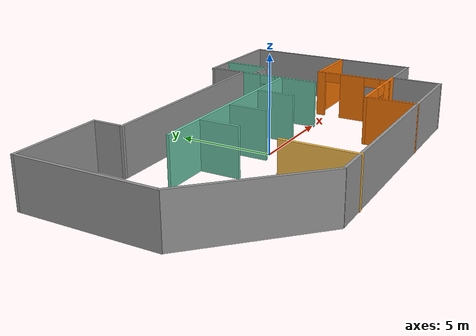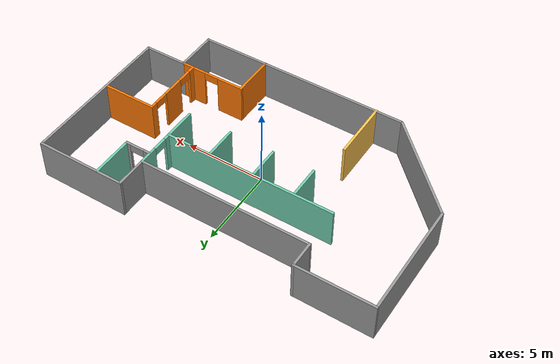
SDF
<?xml version='1.0'?>
<sdf version='1.6'>
  <model name='Building'>
    <link name='Wall_11'>
      <pose frame=''>1.2 -6.05 0 0 -0 0</pose>
      <self_collide>0</self_collide>
      <kinematic>0</kinematic>
      <gravity>1</gravity>
      <inertial>
        <mass>1</mass>
        <pose frame=''>0 0 0 0 -0 0</pose>
        <inertia>
          <ixx>1</ixx>
          <ixy>0</ixy>
          <ixz>0</ixz>
          <iyy>1</iyy>
          <iyz>0</iyz>
          <izz>1</izz>
        </inertia>
      </inertial>
      <visual name='Wall_11_Visual'>
        <pose frame=''>0 0 1.25 0 -0 0</pose>
        <geometry>
          <box>
            <size>13.3 0.15 2.5</size>
          </box>
        </geometry>
        <material>
          <script>
            <uri>file://media/materials/scripts/gazebo.material</uri>
            <name>Gazebo/Grey</name>
          </script>
          <ambient>1 1 1 1</ambient>
          <shader type='pixel'>
            <normal_map>__default__</normal_map>
          </shader>
          <diffuse>0.7 0.7 0.7 1</diffuse>
          <specular>0.01 0.01 0.01 1</specular>
          <emissive>0 0 0 1</emissive>
        </material>
        <meta>
          <layer>0</layer>
        </meta>
        <transparency>0</transparency>
        <cast_shadows>1</cast_shadows>
      </visual>
      <collision name='Wall_11_Collision'>
        <laser_retro>0</laser_retro>
        <max_contacts>10</max_contacts>
        <pose frame=''>0 0 1.25 0 -0 0</pose>
        <geometry>
          <box>
            <size>13.3 0.15 2.5</size>
          </box>
        </geometry>
        <surface>
          <friction>
            <ode>
              <mu>1</mu>
              <mu2>1</mu2>
              <fdir1>0 0 0</fdir1>
              <slip1>0</slip1>
              <slip2>0</slip2>
            </ode>
            <torsional>
              <coefficient>1</coefficient>
              <patch_radius>0</patch_radius>
              <surface_radius>0</surface_radius>
              <use_patch_radius>1</use_patch_radius>
              <ode>
                <slip>0</slip>
              </ode>
            </torsional>
          </friction>
          <bounce>
            <restitution_coefficient>0</restitution_coefficient>
            <threshold>1e+06</threshold>
          </bounce>
          <contact>
            <collide_without_contact>0</collide_without_contact>
            <collide_without_contact_bitmask>1</collide_without_contact_bitmask>
            <collide_bitmask>1</collide_bitmask>
            <ode>
              <soft_cfm>0</soft_cfm>
              <soft_erp>0.2</soft_erp>
              <kp>1e+13</kp>
              <kd>1</kd>
              <max_vel>0.01</max_vel>
              <min_depth>0</min_depth>
            </ode>
            <bullet>
              <split_impulse>1</split_impulse>
              <split_impulse_penetration_threshold>-0.01</split_impulse_penetration_threshold>
              <soft_cfm>0</soft_cfm>
              <soft_erp>0.2</soft_erp>
              <kp>1e+13</kp>
              <kd>1</kd>
            </bullet>
          </contact>
        </surface>
      </collision>
    </link>
    <link name='Wall_114'>
      <pose frame=''>5.74685 3.602 0 0 -0 0</pose>
      <self_collide>0</self_collide>
      <kinematic>0</kinematic>
      <visual name='Wall_114_Visual_0'>
        <pose frame=''>-0.620125 0 1.25 0 -0 0</pose>
        <geometry>
          <box>
            <size>0.409749 0.15 2.5</size>
          </box>
        </geometry>
        <material>
          <script>
            <uri>file://media/materials/scripts/gazebo.material</uri>
            <name>Gazebo/Grey</name>
          </script>
          <ambient>1 1 1 1</ambient>
          <shader type='pixel'/>
          <diffuse>0.7 0.7 0.7 1</diffuse>
          <specular>0.01 0.01 0.01 1</specular>
          <emissive>0 0 0 1</emissive>
        </material>
        <meta>
          <layer>0</layer>
        </meta>
        <transparency>0</transparency>
        <cast_shadows>1</cast_shadows>
      </visual>
      <visual name='Wall_114_Visual_1'>
        <pose frame=''>0.654875 0 1.25 0 -0 0</pose>
        <geometry>
          <box>
            <size>0.340251 0.15 2.5</size>
          </box>
        </geometry>
        <material>
          <script>
            <uri>file://media/materials/scripts/gazebo.material</uri>
            <name>Gazebo/Grey</name>
          </script>
          <ambient>1 1 1 1</ambient>
          <shader type='pixel'/>
          <diffuse>0.7 0.7 0.7 1</diffuse>
          <specular>0.01 0.01 0.01 1</specular>
          <emissive>0 0 0 1</emissive>
        </material>
        <meta>
          <layer>0</layer>
        </meta>
        <transparency>0</transparency>
        <cast_shadows>1</cast_shadows>
      </visual>
      <visual name='Wall_114_Visual_2'>
        <pose frame=''>0.034749 0 2.25 0 -0 0</pose>
        <geometry>
          <box>
            <size>0.9 0.15 0.5</size>
          </box>
        </geometry>
        <material>
          <script>
            <uri>file://media/materials/scripts/gazebo.material</uri>
            <name>Gazebo/Grey</name>
          </script>
          <ambient>1 1 1 1</ambient>
          <shader type='pixel'/>
          <diffuse>0.7 0.7 0.7 1</diffuse>
          <specular>0.01 0.01 0.01 1</specular>
          <emissive>0 0 0 1</emissive>
        </material>
        <meta>
          <layer>0</layer>
        </meta>
        <transparency>0</transparency>
        <cast_shadows>1</cast_shadows>
      </visual>
      <collision name='Wall_114_Collision_0'>
        <laser_retro>0</laser_retro>
        <max_contacts>10</max_contacts>
        <pose frame=''>-0.620125 0 1.25 0 -0 0</pose>
        <geometry>
          <box>
            <size>0.409749 0.15 2.5</size>
          </box>
        </geometry>
        <surface>
          <friction>
            <ode>
              <mu>1</mu>
              <mu2>1</mu2>
              <fdir1>0 0 0</fdir1>
              <slip1>0</slip1>
              <slip2>0</slip2>
            </ode>
            <torsional>
              <coefficient>1</coefficient>
              <patch_radius>0</patch_radius>
              <surface_radius>0</surface_radius>
              <use_patch_radius>1</use_patch_radius>
              <ode>
                <slip>0</slip>
              </ode>
            </torsional>
          </friction>
          <bounce>
            <restitution_coefficient>0</restitution_coefficient>
            <threshold>1e+06</threshold>
          </bounce>
          <contact>
            <collide_without_contact>0</collide_without_contact>
            <collide_without_contact_bitmask>1</collide_without_contact_bitmask>
            <collide_bitmask>1</collide_bitmask>
            <ode>
              <soft_cfm>0</soft_cfm>
              <soft_erp>0.2</soft_erp>
              <kp>1e+13</kp>
              <kd>1</kd>
              <max_vel>0.01</max_vel>
              <min_depth>0</min_depth>
            </ode>
            <bullet>
              <split_impulse>1</split_impulse>
              <split_impulse_penetration_threshold>-0.01</split_impulse_penetration_threshold>
              <soft_cfm>0</soft_cfm>
              <soft_erp>0.2</soft_erp>
              <kp>1e+13</kp>
              <kd>1</kd>
            </bullet>
          </contact>
        </surface>
      </collision>
      <collision name='Wall_114_Collision_1'>
        <laser_retro>0</laser_retro>
        <max_contacts>10</max_contacts>
        <pose frame=''>0.654875 0 1.25 0 -0 0</pose>
        <geometry>
          <box>
            <size>0.340251 0.15 2.5</size>
          </box>
        </geometry>
        <surface>
          <friction>
            <ode>
              <mu>1</mu>
              <mu2>1</mu2>
              <fdir1>0 0 0</fdir1>
              <slip1>0</slip1>
              <slip2>0</slip2>
            </ode>
            <torsional>
              <coefficient>1</coefficient>
              <patch_radius>0</patch_radius>
              <surface_radius>0</surface_radius>
              <use_patch_radius>1</use_patch_radius>
              <ode>
                <slip>0</slip>
              </ode>
            </torsional>
          </friction>
          <bounce>
            <restitution_coefficient>0</restitution_coefficient>
            <threshold>1e+06</threshold>
          </bounce>
          <contact>
            <collide_without_contact>0</collide_without_contact>
            <collide_without_contact_bitmask>1</collide_without_contact_bitmask>
            <collide_bitmask>1</collide_bitmask>
            <ode>
              <soft_cfm>0</soft_cfm>
              <soft_erp>0.2</soft_erp>
              <kp>1e+13</kp>
              <kd>1</kd>
              <max_vel>0.01</max_vel>
              <min_depth>0</min_depth>
            </ode>
            <bullet>
              <split_impulse>1</split_impulse>
              <split_impulse_penetration_threshold>-0.01</split_impulse_penetration_threshold>
              <soft_cfm>0</soft_cfm>
              <soft_erp>0.2</soft_erp>
              <kp>1e+13</kp>
              <kd>1</kd>
            </bullet>
          </contact>
        </surface>
      </collision>
      <collision name='Wall_114_Collision_2'>
        <laser_retro>0</laser_retro>
        <max_contacts>10</max_contacts>
        <pose frame=''>0.034749 0 2.25 0 -0 0</pose>
        <geometry>
          <box>
            <size>0.9 0.15 0.5</size>
          </box>
        </geometry>
        <surface>
          <friction>
            <ode>
              <mu>1</mu>
              <mu2>1</mu2>
              <fdir1>0 0 0</fdir1>
              <slip1>0</slip1>
              <slip2>0</slip2>
            </ode>
            <torsional>
              <coefficient>1</coefficient>
              <patch_radius>0</patch_radius>
              <surface_radius>0</surface_radius>
              <use_patch_radius>1</use_patch_radius>
              <ode>
                <slip>0</slip>
              </ode>
            </torsional>
          </friction>
          <bounce>
            <restitution_coefficient>0</restitution_coefficient>
            <threshold>1e+06</threshold>
          </bounce>
          <contact>
            <collide_without_contact>0</collide_without_contact>
            <collide_without_contact_bitmask>1</collide_without_contact_bitmask>
            <collide_bitmask>1</collide_bitmask>
            <ode>
              <soft_cfm>0</soft_cfm>
              <soft_erp>0.2</soft_erp>
              <kp>1e+13</kp>
              <kd>1</kd>
              <max_vel>0.01</max_vel>
              <min_depth>0</min_depth>
            </ode>
            <bullet>
              <split_impulse>1</split_impulse>
              <split_impulse_penetration_threshold>-0.01</split_impulse_penetration_threshold>
              <soft_cfm>0</soft_cfm>
              <soft_erp>0.2</soft_erp>
              <kp>1e+13</kp>
              <kd>1</kd>
            </bullet>
          </contact>
        </surface>
      </collision>
    </link>
    <link name='Wall_116'>
      <pose frame=''>6.50779 4.9025 0 0 -0 1.5708</pose>
      <self_collide>0</self_collide>
      <kinematic>0</kinematic>
      <visual name='Wall_116_Visual'>
        <pose frame=''>0 0 1.25 0 -0 0</pose>
        <geometry>
          <box>
            <size>2.75 0.15 2.5</size>
          </box>
        </geometry>
        <material>
          <script>
            <uri>file://media/materials/scripts/gazebo.material</uri>
            <name>Gazebo/Grey</name>
          </script>
          <ambient>0.435294 0.796078 0.67451 1</ambient>
          <shader type='pixel'/>
          <diffuse>0.7 0.7 0.7 1</diffuse>
          <specular>0.01 0.01 0.01 1</specular>
          <emissive>0 0 0 1</emissive>
        </material>
        <meta>
          <layer>0</layer>
        </meta>
        <transparency>0</transparency>
        <cast_shadows>1</cast_shadows>
      </visual>
      <collision name='Wall_116_Collision'>
        <laser_retro>0</laser_retro>
        <max_contacts>10</max_contacts>
        <pose frame=''>0 0 1.25 0 -0 0</pose>
        <geometry>
          <box>
            <size>2.75 0.15 2.5</size>
          </box>
        </geometry>
        <surface>
          <friction>
            <ode>
              <mu>1</mu>
              <mu2>1</mu2>
              <fdir1>0 0 0</fdir1>
              <slip1>0</slip1>
              <slip2>0</slip2>
            </ode>
            <torsional>
              <coefficient>1</coefficient>
              <patch_radius>0</patch_radius>
              <surface_radius>0</surface_radius>
              <use_patch_radius>1</use_patch_radius>
              <ode>
                <slip>0</slip>
              </ode>
            </torsional>
          </friction>
          <bounce>
            <restitution_coefficient>0</restitution_coefficient>
            <threshold>1e+06</threshold>
          </bounce>
          <contact>
            <collide_without_contact>0</collide_without_contact>
            <collide_without_contact_bitmask>1</collide_without_contact_bitmask>
            <collide_bitmask>1</collide_bitmask>
            <ode>
              <soft_cfm>0</soft_cfm>
              <soft_erp>0.2</soft_erp>
              <kp>1e+13</kp>
              <kd>1</kd>
              <max_vel>0.01</max_vel>
              <min_depth>0</min_depth>
            </ode>
            <bullet>
              <split_impulse>1</split_impulse>
              <split_impulse_penetration_threshold>-0.01</split_impulse_penetration_threshold>
              <soft_cfm>0</soft_cfm>
              <soft_erp>0.2</soft_erp>
              <kp>1e+13</kp>
              <kd>1</kd>
            </bullet>
          </contact>
        </surface>
      </collision>
    </link>
    <link name='Wall_120'>
      <pose frame=''>7.77481 -4.83428 0 0 -0 1.57077</pose>
      <self_collide>0</self_collide>
      <kinematic>0</kinematic>
      <gravity>1</gravity>
      <inertial>
        <mass>1</mass>
        <pose frame=''>0 0 0 0 -0 0</pose>
        <inertia>
          <ixx>1</ixx>
          <ixy>0</ixy>
          <ixz>0</ixz>
          <iyy>1</iyy>
          <iyz>0</iyz>
          <izz>1</izz>
        </inertia>
      </inertial>
      <visual name='Wall_120_Visual'>
        <pose frame=''>0 0 1.25 0 -0 0</pose>
        <geometry>
          <box>
            <size>2.6 0.15 2.5</size>
          </box>
        </geometry>
        <material>
          <script>
            <uri>file://media/materials/scripts/gazebo.material</uri>
            <name>Gazebo/Grey</name>
          </script>
          <ambient>1 1 1 1</ambient>
          <shader type='pixel'>
            <normal_map>__default__</normal_map>
          </shader>
          <diffuse>0.7 0.7 0.7 1</diffuse>
          <specular>0.01 0.01 0.01 1</specular>
          <emissive>0 0 0 1</emissive>
        </material>
        <meta>
          <layer>0</layer>
        </meta>
        <transparency>0</transparency>
        <cast_shadows>1</cast_shadows>
      </visual>
      <collision name='Wall_120_Collision'>
        <laser_retro>0</laser_retro>
        <max_contacts>10</max_contacts>
        <pose frame=''>0 0 1.25 0 -0 0</pose>
        <geometry>
          <box>
            <size>2.6 0.15 2.5</size>
          </box>
        </geometry>
        <surface>
          <friction>
            <ode>
              <mu>1</mu>
              <mu2>1</mu2>
              <fdir1>0 0 0</fdir1>
              <slip1>0</slip1>
              <slip2>0</slip2>
            </ode>
            <torsional>
              <coefficient>1</coefficient>
              <patch_radius>0</patch_radius>
              <surface_radius>0</surface_radius>
              <use_patch_radius>1</use_patch_radius>
              <ode>
                <slip>0</slip>
              </ode>
            </torsional>
          </friction>
          <bounce>
            <restitution_coefficient>0</restitution_coefficient>
            <threshold>1e+06</threshold>
          </bounce>
          <contact>
            <collide_without_contact>0</collide_without_contact>
            <collide_without_contact_bitmask>1</collide_without_contact_bitmask>
            <collide_bitmask>1</collide_bitmask>
            <ode>
              <soft_cfm>0</soft_cfm>
              <soft_erp>0.2</soft_erp>
              <kp>1e+13</kp>
              <kd>1</kd>
              <max_vel>0.01</max_vel>
              <min_depth>0</min_depth>
            </ode>
            <bullet>
              <split_impulse>1</split_impulse>
              <split_impulse_penetration_threshold>-0.01</split_impulse_penetration_threshold>
              <soft_cfm>0</soft_cfm>
              <soft_erp>0.2</soft_erp>
              <kp>1e+13</kp>
              <kd>1</kd>
            </bullet>
          </contact>
        </surface>
      </collision>
    </link>
    <link name='Wall_122'>
      <pose frame=''>7.07785 -1.4415 0 0 -0 1.5708</pose>
      <self_collide>0</self_collide>
      <kinematic>0</kinematic>
      <visual name='Wall_122_Visual_0'>
        <pose frame=''>-1.82998 0 1.25 0 -0 0</pose>
        <geometry>
          <box>
            <size>0.532998 0.15 2.5</size>
          </box>
        </geometry>
        <material>
          <script>
            <uri>file://media/materials/scripts/gazebo.material</uri>
            <name>Gazebo/Grey</name>
          </script>
          <ambient>0.996078 0.47451 0.0196078 1</ambient>
          <shader type='pixel'/>
          <diffuse>0.7 0.7 0.7 1</diffuse>
          <specular>0.01 0.01 0.01 1</specular>
          <emissive>0 0 0 1</emissive>
        </material>
        <meta>
          <layer>0</layer>
        </meta>
        <transparency>0</transparency>
        <cast_shadows>1</cast_shadows>
      </visual>
      <visual name='Wall_122_Visual_1'>
        <pose frame=''>0.029829 0 1.25 0 -0 0</pose>
        <geometry>
          <box>
            <size>1.38662 0.15 2.5</size>
          </box>
        </geometry>
        <material>
          <script>
            <uri>file://media/materials/scripts/gazebo.material</uri>
            <name>Gazebo/Grey</name>
          </script>
          <ambient>0.996078 0.47451 0.0196078 1</ambient>
          <shader type='pixel'/>
          <diffuse>0.7 0.7 0.7 1</diffuse>
          <specular>0.01 0.01 0.01 1</specular>
          <emissive>0 0 0 1</emissive>
        </material>
        <meta>
          <layer>0</layer>
        </meta>
        <transparency>0</transparency>
        <cast_shadows>1</cast_shadows>
      </visual>
      <visual name='Wall_122_Visual_2'>
        <pose frame=''>1.85981 0 1.25 0 -0 0</pose>
        <geometry>
          <box>
            <size>0.473341 0.15 2.5</size>
          </box>
        </geometry>
        <material>
          <script>
            <uri>file://media/materials/scripts/gazebo.material</uri>
            <name>Gazebo/Grey</name>
          </script>
          <ambient>0.996078 0.47451 0.0196078 1</ambient>
          <shader type='pixel'/>
          <diffuse>0.7 0.7 0.7 1</diffuse>
          <specular>0.01 0.01 0.01 1</specular>
          <emissive>0 0 0 1</emissive>
        </material>
        <meta>
          <layer>0</layer>
        </meta>
        <transparency>0</transparency>
        <cast_shadows>1</cast_shadows>
      </visual>
      <visual name='Wall_122_Visual_3'>
        <pose frame=''>-1.11348 0 2.25 0 -0 0</pose>
        <geometry>
          <box>
            <size>0.9 0.15 0.5</size>
          </box>
        </geometry>
        <material>
          <script>
            <uri>file://media/materials/scripts/gazebo.material</uri>
            <name>Gazebo/Grey</name>
          </script>
          <ambient>0.996078 0.47451 0.0196078 1</ambient>
          <shader type='pixel'/>
          <diffuse>0.7 0.7 0.7 1</diffuse>
          <specular>0.01 0.01 0.01 1</specular>
          <emissive>0 0 0 1</emissive>
        </material>
        <meta>
          <layer>0</layer>
        </meta>
        <transparency>0</transparency>
        <cast_shadows>1</cast_shadows>
      </visual>
      <visual name='Wall_122_Visual_4'>
        <pose frame=''>1.17314 0 2.25 0 -0 0</pose>
        <geometry>
          <box>
            <size>0.9 0.15 0.5</size>
          </box>
        </geometry>
        <material>
          <script>
            <uri>file://media/materials/scripts/gazebo.material</uri>
            <name>Gazebo/Grey</name>
          </script>
          <ambient>0.996078 0.47451 0.0196078 1</ambient>
          <shader type='pixel'/>
          <diffuse>0.7 0.7 0.7 1</diffuse>
          <specular>0.01 0.01 0.01 1</specular>
          <emissive>0 0 0 1</emissive>
        </material>
        <meta>
          <layer>0</layer>
        </meta>
        <transparency>0</transparency>
        <cast_shadows>1</cast_shadows>
      </visual>
      <collision name='Wall_122_Collision_0'>
        <laser_retro>0</laser_retro>
        <max_contacts>10</max_contacts>
        <pose frame=''>-1.82998 0 1.25 0 -0 0</pose>
        <geometry>
          <box>
            <size>0.532998 0.15 2.5</size>
          </box>
        </geometry>
        <surface>
          <friction>
            <ode>
              <mu>1</mu>
              <mu2>1</mu2>
              <fdir1>0 0 0</fdir1>
              <slip1>0</slip1>
              <slip2>0</slip2>
            </ode>
            <torsional>
              <coefficient>1</coefficient>
              <patch_radius>0</patch_radius>
              <surface_radius>0</surface_radius>
              <use_patch_radius>1</use_patch_radius>
              <ode>
                <slip>0</slip>
              </ode>
            </torsional>
          </friction>
          <bounce>
            <restitution_coefficient>0</restitution_coefficient>
            <threshold>1e+06</threshold>
          </bounce>
          <contact>
            <collide_without_contact>0</collide_without_contact>
            <collide_without_contact_bitmask>1</collide_without_contact_bitmask>
            <collide_bitmask>1</collide_bitmask>
            <ode>
              <soft_cfm>0</soft_cfm>
              <soft_erp>0.2</soft_erp>
              <kp>1e+13</kp>
              <kd>1</kd>
              <max_vel>0.01</max_vel>
              <min_depth>0</min_depth>
            </ode>
            <bullet>
              <split_impulse>1</split_impulse>
              <split_impulse_penetration_threshold>-0.01</split_impulse_penetration_threshold>
              <soft_cfm>0</soft_cfm>
              <soft_erp>0.2</soft_erp>
              <kp>1e+13</kp>
              <kd>1</kd>
            </bullet>
          </contact>
        </surface>
      </collision>
      <collision name='Wall_122_Collision_1'>
        <laser_retro>0</laser_retro>
        <max_contacts>10</max_contacts>
        <pose frame=''>0.029829 0 1.25 0 -0 0</pose>
        <geometry>
          <box>
            <size>1.38662 0.15 2.5</size>
          </box>
        </geometry>
        <surface>
          <friction>
            <ode>
              <mu>1</mu>
              <mu2>1</mu2>
              <fdir1>0 0 0</fdir1>
              <slip1>0</slip1>
              <slip2>0</slip2>
            </ode>
            <torsional>
              <coefficient>1</coefficient>
              <patch_radius>0</patch_radius>
              <surface_radius>0</surface_radius>
              <use_patch_radius>1</use_patch_radius>
              <ode>
                <slip>0</slip>
              </ode>
            </torsional>
          </friction>
          <bounce>
            <restitution_coefficient>0</restitution_coefficient>
            <threshold>1e+06</threshold>
          </bounce>
          <contact>
            <collide_without_contact>0</collide_without_contact>
            <collide_without_contact_bitmask>1</collide_without_contact_bitmask>
            <collide_bitmask>1</collide_bitmask>
            <ode>
              <soft_cfm>0</soft_cfm>
              <soft_erp>0.2</soft_erp>
              <kp>1e+13</kp>
              <kd>1</kd>
              <max_vel>0.01</max_vel>
              <min_depth>0</min_depth>
            </ode>
            <bullet>
              <split_impulse>1</split_impulse>
              <split_impulse_penetration_threshold>-0.01</split_impulse_penetration_threshold>
              <soft_cfm>0</soft_cfm>
              <soft_erp>0.2</soft_erp>
              <kp>1e+13</kp>
              <kd>1</kd>
            </bullet>
          </contact>
        </surface>
      </collision>
      <collision name='Wall_122_Collision_3'>
        <laser_retro>0</laser_retro>
        <max_contacts>10</max_contacts>
        <pose frame=''>-1.11348 0 2.25 0 -0 0</pose>
        <geometry>
          <box>
            <size>0.9 0.15 0.5</size>
          </box>
        </geometry>
        <surface>
          <friction>
            <ode>
              <mu>1</mu>
              <mu2>1</mu2>
              <fdir1>0 0 0</fdir1>
              <slip1>0</slip1>
              <slip2>0</slip2>
            </ode>
            <torsional>
              <coefficient>1</coefficient>
              <patch_radius>0</patch_radius>
              <surface_radius>0</surface_radius>
              <use_patch_radius>1</use_patch_radius>
              <ode>
                <slip>0</slip>
              </ode>
            </torsional>
          </friction>
          <bounce>
            <restitution_coefficient>0</restitution_coefficient>
            <threshold>1e+06</threshold>
          </bounce>
          <contact>
            <collide_without_contact>0</collide_without_contact>
            <collide_without_contact_bitmask>1</collide_without_contact_bitmask>
            <collide_bitmask>1</collide_bitmask>
            <ode>
              <soft_cfm>0</soft_cfm>
              <soft_erp>0.2</soft_erp>
              <kp>1e+13</kp>
              <kd>1</kd>
              <max_vel>0.01</max_vel>
              <min_depth>0</min_depth>
            </ode>
            <bullet>
              <split_impulse>1</split_impulse>
              <split_impulse_penetration_threshold>-0.01</split_impulse_penetration_threshold>
              <soft_cfm>0</soft_cfm>
              <soft_erp>0.2</soft_erp>
              <kp>1e+13</kp>
              <kd>1</kd>
            </bullet>
          </contact>
        </surface>
      </collision>
      <collision name='Wall_122_Collision_2'>
        <laser_retro>0</laser_retro>
        <max_contacts>10</max_contacts>
        <pose frame=''>1.85981 0 1.25 0 -0 0</pose>
        <geometry>
          <box>
            <size>0.473341 0.15 2.5</size>
          </box>
        </geometry>
        <surface>
          <friction>
            <ode>
              <mu>1</mu>
              <mu2>1</mu2>
              <fdir1>0 0 0</fdir1>
              <slip1>0</slip1>
              <slip2>0</slip2>
            </ode>
            <torsional>
              <coefficient>1</coefficient>
              <patch_radius>0</patch_radius>
              <surface_radius>0</surface_radius>
              <use_patch_radius>1</use_patch_radius>
              <ode>
                <slip>0</slip>
              </ode>
            </torsional>
          </friction>
          <bounce>
            <restitution_coefficient>0</restitution_coefficient>
            <threshold>1e+06</threshold>
          </bounce>
          <contact>
            <collide_without_contact>0</collide_without_contact>
            <collide_without_contact_bitmask>1</collide_without_contact_bitmask>
            <collide_bitmask>1</collide_bitmask>
            <ode>
              <soft_cfm>0</soft_cfm>
              <soft_erp>0.2</soft_erp>
              <kp>1e+13</kp>
              <kd>1</kd>
              <max_vel>0.01</max_vel>
              <min_depth>0</min_depth>
            </ode>
            <bullet>
              <split_impulse>1</split_impulse>
              <split_impulse_penetration_threshold>-0.01</split_impulse_penetration_threshold>
              <soft_cfm>0</soft_cfm>
              <soft_erp>0.2</soft_erp>
              <kp>1e+13</kp>
              <kd>1</kd>
            </bullet>
          </contact>
        </surface>
      </collision>
      <collision name='Wall_122_Collision_4'>
        <laser_retro>0</laser_retro>
        <max_contacts>10</max_contacts>
        <pose frame=''>1.17314 0 2.25 0 -0 0</pose>
        <geometry>
          <box>
            <size>0.9 0.15 0.5</size>
          </box>
        </geometry>
        <surface>
          <friction>
            <ode>
              <mu>1</mu>
              <mu2>1</mu2>
              <fdir1>0 0 0</fdir1>
              <slip1>0</slip1>
              <slip2>0</slip2>
            </ode>
            <torsional>
              <coefficient>1</coefficient>
              <patch_radius>0</patch_radius>
              <surface_radius>0</surface_radius>
              <use_patch_radius>1</use_patch_radius>
              <ode>
                <slip>0</slip>
              </ode>
            </torsional>
          </friction>
          <bounce>
            <restitution_coefficient>0</restitution_coefficient>
            <threshold>1e+06</threshold>
          </bounce>
          <contact>
            <collide_without_contact>0</collide_without_contact>
            <collide_without_contact_bitmask>1</collide_without_contact_bitmask>
            <collide_bitmask>1</collide_bitmask>
            <ode>
              <soft_cfm>0</soft_cfm>
              <soft_erp>0.2</soft_erp>
              <kp>1e+13</kp>
              <kd>1</kd>
              <max_vel>0.01</max_vel>
              <min_depth>0</min_depth>
            </ode>
            <bullet>
              <split_impulse>1</split_impulse>
              <split_impulse_penetration_threshold>-0.01</split_impulse_penetration_threshold>
              <soft_cfm>0</soft_cfm>
              <soft_erp>0.2</soft_erp>
              <kp>1e+13</kp>
              <kd>1</kd>
            </bullet>
          </contact>
        </surface>
      </collision>
    </link>
    <link name='Wall_123'>
      <pose frame=''>8.65985 0.580004 0 0 -0 0</pose>
      <self_collide>0</self_collide>
      <kinematic>0</kinematic>
      <visual name='Wall_123_Visual'>
        <pose frame=''>0 0 1.25 0 -0 0</pose>
        <geometry>
          <box>
            <size>3.314 0.15 2.5</size>
          </box>
        </geometry>
        <material>
          <script>
            <uri>file://media/materials/scripts/gazebo.material</uri>
            <name>Gazebo/Grey</name>
          </script>
          <ambient>0.996078 0.47451 0.0196078 1</ambient>
          <shader type='pixel'/>
          <diffuse>0.7 0.7 0.7 1</diffuse>
          <specular>0.01 0.01 0.01 1</specular>
          <emissive>0 0 0 1</emissive>
        </material>
        <meta>
          <layer>0</layer>
        </meta>
        <transparency>0</transparency>
        <cast_shadows>1</cast_shadows>
      </visual>
      <collision name='Wall_123_Collision'>
        <laser_retro>0</laser_retro>
        <max_contacts>10</max_contacts>
        <pose frame=''>0 0 1.25 0 -0 0</pose>
        <geometry>
          <box>
            <size>3.314 0.15 2.5</size>
          </box>
        </geometry>
        <surface>
          <friction>
            <ode>
              <mu>1</mu>
              <mu2>1</mu2>
              <fdir1>0 0 0</fdir1>
              <slip1>0</slip1>
              <slip2>0</slip2>
            </ode>
            <torsional>
              <coefficient>1</coefficient>
              <patch_radius>0</patch_radius>
              <surface_radius>0</surface_radius>
              <use_patch_radius>1</use_patch_radius>
              <ode>
                <slip>0</slip>
              </ode>
            </torsional>
          </friction>
          <bounce>
            <restitution_coefficient>0</restitution_coefficient>
            <threshold>1e+06</threshold>
          </bounce>
          <contact>
            <collide_without_contact>0</collide_without_contact>
            <collide_without_contact_bitmask>1</collide_without_contact_bitmask>
            <collide_bitmask>1</collide_bitmask>
            <ode>
              <soft_cfm>0</soft_cfm>
              <soft_erp>0.2</soft_erp>
              <kp>1e+13</kp>
              <kd>1</kd>
              <max_vel>0.01</max_vel>
              <min_depth>0</min_depth>
            </ode>
            <bullet>
              <split_impulse>1</split_impulse>
              <split_impulse_penetration_threshold>-0.01</split_impulse_penetration_threshold>
              <soft_cfm>0</soft_cfm>
              <soft_erp>0.2</soft_erp>
              <kp>1e+13</kp>
              <kd>1</kd>
            </bullet>
          </contact>
        </surface>
      </collision>
    </link>
    <link name='Wall_133'>
      <pose frame=''>-3.81217 -4.27997 0 0 0 -1.5708</pose>
      <self_collide>0</self_collide>
      <kinematic>0</kinematic>
      <visual name='Wall_133_Visual'>
        <pose frame=''>0 0 1.25 0 -0 0</pose>
        <geometry>
          <box>
            <size>3.75 0.15 2.5</size>
          </box>
        </geometry>
        <material>
          <script>
            <uri>file://media/materials/scripts/gazebo.material</uri>
            <name>Gazebo/Grey</name>
          </script>
          <ambient>1 0.764706 0.305882 1</ambient>
          <shader type='pixel'/>
          <diffuse>0.7 0.7 0.7 1</diffuse>
          <specular>0.01 0.01 0.01 1</specular>
          <emissive>0 0 0 1</emissive>
        </material>
        <meta>
          <layer>0</layer>
        </meta>
        <transparency>0</transparency>
        <cast_shadows>1</cast_shadows>
      </visual>
      <collision name='Wall_133_Collision'>
        <laser_retro>0</laser_retro>
        <max_contacts>10</max_contacts>
        <pose frame=''>0 0 1.25 0 -0 0</pose>
        <geometry>
          <box>
            <size>3.75 0.15 2.5</size>
          </box>
        </geometry>
        <surface>
          <friction>
            <ode>
              <mu>1</mu>
              <mu2>1</mu2>
              <fdir1>0 0 0</fdir1>
              <slip1>0</slip1>
              <slip2>0</slip2>
            </ode>
            <torsional>
              <coefficient>1</coefficient>
              <patch_radius>0</patch_radius>
              <surface_radius>0</surface_radius>
              <use_patch_radius>1</use_patch_radius>
              <ode>
                <slip>0</slip>
              </ode>
            </torsional>
          </friction>
          <bounce>
            <restitution_coefficient>0</restitution_coefficient>
            <threshold>1e+06</threshold>
          </bounce>
          <contact>
            <collide_without_contact>0</collide_without_contact>
            <collide_without_contact_bitmask>1</collide_without_contact_bitmask>
            <collide_bitmask>1</collide_bitmask>
            <ode>
              <soft_cfm>0</soft_cfm>
              <soft_erp>0.2</soft_erp>
              <kp>1e+13</kp>
              <kd>1</kd>
              <max_vel>0.01</max_vel>
              <min_depth>0</min_depth>
            </ode>
            <bullet>
              <split_impulse>1</split_impulse>
              <split_impulse_penetration_threshold>-0.01</split_impulse_penetration_threshold>
              <soft_cfm>0</soft_cfm>
              <soft_erp>0.2</soft_erp>
              <kp>1e+13</kp>
              <kd>1</kd>
            </bullet>
          </contact>
        </surface>
      </collision>
    </link>
    <link name='Wall_14'>
      <pose frame=''>10.375 1.37771 0 0 -0 1.57083</pose>
      <self_collide>0</self_collide>
      <kinematic>0</kinematic>
      <visual name='Wall_14_Visual'>
        <pose frame=''>0 0 1.25 0 -0 0</pose>
        <geometry>
          <box>
            <size>9.81812 0.15 2.5</size>
          </box>
        </geometry>
        <material>
          <script>
            <uri>file://media/materials/scripts/gazebo.material</uri>
            <name>Gazebo/Grey</name>
          </script>
          <ambient>1 1 1 1</ambient>
          <shader type='pixel'/>
          <diffuse>0.7 0.7 0.7 1</diffuse>
          <specular>0.01 0.01 0.01 1</specular>
          <emissive>0 0 0 1</emissive>
        </material>
        <meta>
          <layer>0</layer>
        </meta>
        <transparency>0</transparency>
        <cast_shadows>1</cast_shadows>
      </visual>
      <collision name='Wall_14_Collision'>
        <laser_retro>0</laser_retro>
        <max_contacts>10</max_contacts>
        <pose frame=''>0 0 1.25 0 -0 0</pose>
        <geometry>
          <box>
            <size>9.81812 0.15 2.5</size>
          </box>
        </geometry>
        <surface>
          <friction>
            <ode>
              <mu>1</mu>
              <mu2>1</mu2>
              <fdir1>0 0 0</fdir1>
              <slip1>0</slip1>
              <slip2>0</slip2>
            </ode>
            <torsional>
              <coefficient>1</coefficient>
              <patch_radius>0</patch_radius>
              <surface_radius>0</surface_radius>
              <use_patch_radius>1</use_patch_radius>
              <ode>
                <slip>0</slip>
              </ode>
            </torsional>
          </friction>
          <bounce>
            <restitution_coefficient>0</restitution_coefficient>
            <threshold>1e+06</threshold>
          </bounce>
          <contact>
            <collide_without_contact>0</collide_without_contact>
            <collide_without_contact_bitmask>1</collide_without_contact_bitmask>
            <collide_bitmask>1</collide_bitmask>
            <ode>
              <soft_cfm>0</soft_cfm>
              <soft_erp>0.2</soft_erp>
              <kp>1e+13</kp>
              <kd>1</kd>
              <max_vel>0.01</max_vel>
              <min_depth>0</min_depth>
            </ode>
            <bullet>
              <split_impulse>1</split_impulse>
              <split_impulse_penetration_threshold>-0.01</split_impulse_penetration_threshold>
              <soft_cfm>0</soft_cfm>
              <soft_erp>0.2</soft_erp>
              <kp>1e+13</kp>
              <kd>1</kd>
            </bullet>
          </contact>
        </surface>
      </collision>
    </link>
    <link name='Wall_140'>
      <pose frame=''>9.07503 -3.45679 0 0 0 -3.14144</pose>
      <self_collide>0</self_collide>
      <kinematic>0</kinematic>
      <visual name='Wall_140_Visual'>
        <pose frame=''>0 0 1.25 0 -0 0</pose>
        <geometry>
          <box>
            <size>2.75 0.15 2.5</size>
          </box>
        </geometry>
        <material>
          <script>
            <uri>file://media/materials/scripts/gazebo.material</uri>
            <name>Gazebo/Grey</name>
          </script>
          <ambient>1 1 1 1</ambient>
          <shader type='pixel'/>
          <diffuse>0.7 0.7 0.7 1</diffuse>
          <specular>0.01 0.01 0.01 1</specular>
          <emissive>0 0 0 1</emissive>
        </material>
        <meta>
          <layer>0</layer>
        </meta>
        <transparency>0</transparency>
        <cast_shadows>1</cast_shadows>
      </visual>
      <collision name='Wall_140_Collision'>
        <laser_retro>0</laser_retro>
        <max_contacts>10</max_contacts>
        <pose frame=''>0 0 1.25 0 -0 0</pose>
        <geometry>
          <box>
            <size>2.75 0.15 2.5</size>
          </box>
        </geometry>
        <surface>
          <friction>
            <ode>
              <mu>1</mu>
              <mu2>1</mu2>
              <fdir1>0 0 0</fdir1>
              <slip1>0</slip1>
              <slip2>0</slip2>
            </ode>
            <torsional>
              <coefficient>1</coefficient>
              <patch_radius>0</patch_radius>
              <surface_radius>0</surface_radius>
              <use_patch_radius>1</use_patch_radius>
              <ode>
                <slip>0</slip>
              </ode>
            </torsional>
          </friction>
          <bounce>
            <restitution_coefficient>0</restitution_coefficient>
            <threshold>1e+06</threshold>
          </bounce>
          <contact>
            <collide_without_contact>0</collide_without_contact>
            <collide_without_contact_bitmask>1</collide_without_contact_bitmask>
            <collide_bitmask>1</collide_bitmask>
            <ode>
              <soft_cfm>0</soft_cfm>
              <soft_erp>0.2</soft_erp>
              <kp>1e+13</kp>
              <kd>1</kd>
              <max_vel>0.01</max_vel>
              <min_depth>0</min_depth>
            </ode>
            <bullet>
              <split_impulse>1</split_impulse>
              <split_impulse_penetration_threshold>-0.01</split_impulse_penetration_threshold>
              <soft_cfm>0</soft_cfm>
              <soft_erp>0.2</soft_erp>
              <kp>1e+13</kp>
              <kd>1</kd>
            </bullet>
          </contact>
        </surface>
      </collision>
    </link>
    <link name='Wall_144'>
      <pose frame=''>5.72485 -3.457 0 0 -0 3.14159</pose>
      <self_collide>0</self_collide>
      <kinematic>0</kinematic>
      <visual name='Wall_144_Visual_0'>
        <pose frame=''>-1.29414 0 1.25 0 -0 0</pose>
        <geometry>
          <box>
            <size>1.66172 0.15 2.5</size>
          </box>
        </geometry>
        <material>
          <script>
            <uri>file://media/materials/scripts/gazebo.material</uri>
            <name>Gazebo/Grey</name>
          </script>
          <ambient>0.996078 0.47451 0.0196078 1</ambient>
          <shader type='pixel'/>
          <diffuse>0.7 0.7 0.7 1</diffuse>
          <specular>0.01 0.01 0.01 1</specular>
          <emissive>0 0 0 1</emissive>
        </material>
        <meta>
          <layer>0</layer>
        </meta>
        <transparency>0</transparency>
        <cast_shadows>1</cast_shadows>
      </visual>
      <visual name='Wall_144_Visual_1'>
        <pose frame=''>1.28086 0 1.25 0 -0 0</pose>
        <geometry>
          <box>
            <size>1.68829 0.15 2.5</size>
          </box>
        </geometry>
        <material>
          <script>
            <uri>file://media/materials/scripts/gazebo.material</uri>
            <name>Gazebo/Grey</name>
          </script>
          <ambient>0.996078 0.47451 0.0196078 1</ambient>
          <shader type='pixel'/>
          <diffuse>0.7 0.7 0.7 1</diffuse>
          <specular>0.01 0.01 0.01 1</specular>
          <emissive>0 0 0 1</emissive>
        </material>
        <meta>
          <layer>0</layer>
        </meta>
        <transparency>0</transparency>
        <cast_shadows>1</cast_shadows>
      </visual>
      <visual name='Wall_144_Visual_2'>
        <pose frame=''>-0.013285 0 2.25 0 -0 0</pose>
        <geometry>
          <box>
            <size>0.9 0.15 0.5</size>
          </box>
        </geometry>
        <material>
          <script>
            <uri>file://media/materials/scripts/gazebo.material</uri>
            <name>Gazebo/Grey</name>
          </script>
          <ambient>0.996078 0.47451 0.0196078 1</ambient>
          <shader type='pixel'/>
          <diffuse>0.7 0.7 0.7 1</diffuse>
          <specular>0.01 0.01 0.01 1</specular>
          <emissive>0 0 0 1</emissive>
        </material>
        <meta>
          <layer>0</layer>
        </meta>
        <transparency>0</transparency>
        <cast_shadows>1</cast_shadows>
      </visual>
      <collision name='Wall_144_Collision_0'>
        <laser_retro>0</laser_retro>
        <max_contacts>10</max_contacts>
        <pose frame=''>-1.29414 0 1.25 0 -0 0</pose>
        <geometry>
          <box>
            <size>1.66172 0.15 2.5</size>
          </box>
        </geometry>
        <surface>
          <friction>
            <ode>
              <mu>1</mu>
              <mu2>1</mu2>
              <fdir1>0 0 0</fdir1>
              <slip1>0</slip1>
              <slip2>0</slip2>
            </ode>
            <torsional>
              <coefficient>1</coefficient>
              <patch_radius>0</patch_radius>
              <surface_radius>0</surface_radius>
              <use_patch_radius>1</use_patch_radius>
              <ode>
                <slip>0</slip>
              </ode>
            </torsional>
          </friction>
          <bounce>
            <restitution_coefficient>0</restitution_coefficient>
            <threshold>1e+06</threshold>
          </bounce>
          <contact>
            <collide_without_contact>0</collide_without_contact>
            <collide_without_contact_bitmask>1</collide_without_contact_bitmask>
            <collide_bitmask>1</collide_bitmask>
            <ode>
              <soft_cfm>0</soft_cfm>
              <soft_erp>0.2</soft_erp>
              <kp>1e+13</kp>
              <kd>1</kd>
              <max_vel>0.01</max_vel>
              <min_depth>0</min_depth>
            </ode>
            <bullet>
              <split_impulse>1</split_impulse>
              <split_impulse_penetration_threshold>-0.01</split_impulse_penetration_threshold>
              <soft_cfm>0</soft_cfm>
              <soft_erp>0.2</soft_erp>
              <kp>1e+13</kp>
              <kd>1</kd>
            </bullet>
          </contact>
        </surface>
      </collision>
      <collision name='Wall_144_Collision_1'>
        <laser_retro>0</laser_retro>
        <max_contacts>10</max_contacts>
        <pose frame=''>1.28086 0 1.25 0 -0 0</pose>
        <geometry>
          <box>
            <size>1.68829 0.15 2.5</size>
          </box>
        </geometry>
        <surface>
          <friction>
            <ode>
              <mu>1</mu>
              <mu2>1</mu2>
              <fdir1>0 0 0</fdir1>
              <slip1>0</slip1>
              <slip2>0</slip2>
            </ode>
            <torsional>
              <coefficient>1</coefficient>
              <patch_radius>0</patch_radius>
              <surface_radius>0</surface_radius>
              <use_patch_radius>1</use_patch_radius>
              <ode>
                <slip>0</slip>
              </ode>
            </torsional>
          </friction>
          <bounce>
            <restitution_coefficient>0</restitution_coefficient>
            <threshold>1e+06</threshold>
          </bounce>
          <contact>
            <collide_without_contact>0</collide_without_contact>
            <collide_without_contact_bitmask>1</collide_without_contact_bitmask>
            <collide_bitmask>1</collide_bitmask>
            <ode>
              <soft_cfm>0</soft_cfm>
              <soft_erp>0.2</soft_erp>
              <kp>1e+13</kp>
              <kd>1</kd>
              <max_vel>0.01</max_vel>
              <min_depth>0</min_depth>
            </ode>
            <bullet>
              <split_impulse>1</split_impulse>
              <split_impulse_penetration_threshold>-0.01</split_impulse_penetration_threshold>
              <soft_cfm>0</soft_cfm>
              <soft_erp>0.2</soft_erp>
              <kp>1e+13</kp>
              <kd>1</kd>
            </bullet>
          </contact>
        </surface>
      </collision>
      <collision name='Wall_144_Collision_2'>
        <laser_retro>0</laser_retro>
        <max_contacts>10</max_contacts>
        <pose frame=''>-0.013285 0 2.25 0 -0 0</pose>
        <geometry>
          <box>
            <size>0.9 0.15 0.5</size>
          </box>
        </geometry>
        <surface>
          <friction>
            <ode>
              <mu>1</mu>
              <mu2>1</mu2>
              <fdir1>0 0 0</fdir1>
              <slip1>0</slip1>
              <slip2>0</slip2>
            </ode>
            <torsional>
              <coefficient>1</coefficient>
              <patch_radius>0</patch_radius>
              <surface_radius>0</surface_radius>
              <use_patch_radius>1</use_patch_radius>
              <ode>
                <slip>0</slip>
              </ode>
            </torsional>
          </friction>
          <bounce>
            <restitution_coefficient>0</restitution_coefficient>
            <threshold>1e+06</threshold>
          </bounce>
          <contact>
            <collide_without_contact>0</collide_without_contact>
            <collide_without_contact_bitmask>1</collide_without_contact_bitmask>
            <collide_bitmask>1</collide_bitmask>
            <ode>
              <soft_cfm>0</soft_cfm>
              <soft_erp>0.2</soft_erp>
              <kp>1e+13</kp>
              <kd>1</kd>
              <max_vel>0.01</max_vel>
              <min_depth>0</min_depth>
            </ode>
            <bullet>
              <split_impulse>1</split_impulse>
              <split_impulse_penetration_threshold>-0.01</split_impulse_penetration_threshold>
              <soft_cfm>0</soft_cfm>
              <soft_erp>0.2</soft_erp>
              <kp>1e+13</kp>
              <kd>1</kd>
            </bullet>
          </contact>
        </surface>
      </collision>
    </link>
    <link name='Wall_145'>
      <pose frame=''>3.67485 -4.757 0 0 0 -1.5708</pose>
      <self_collide>0</self_collide>
      <kinematic>0</kinematic>
      <visual name='Wall_145_Visual'>
        <pose frame=''>0 0 1.25 0 -0 0</pose>
        <geometry>
          <box>
            <size>2.75 0.15 2.5</size>
          </box>
        </geometry>
        <material>
          <script>
            <uri>file://media/materials/scripts/gazebo.material</uri>
            <name>Gazebo/Grey</name>
          </script>
          <ambient>0.996078 0.47451 0.0196078 1</ambient>
          <shader type='pixel'/>
          <diffuse>0.7 0.7 0.7 1</diffuse>
          <specular>0.01 0.01 0.01 1</specular>
          <emissive>0 0 0 1</emissive>
        </material>
        <meta>
          <layer>0</layer>
        </meta>
        <transparency>0</transparency>
        <cast_shadows>1</cast_shadows>
      </visual>
      <collision name='Wall_145_Collision'>
        <laser_retro>0</laser_retro>
        <max_contacts>10</max_contacts>
        <pose frame=''>0 0 1.25 0 -0 0</pose>
        <geometry>
          <box>
            <size>2.75 0.15 2.5</size>
          </box>
        </geometry>
        <surface>
          <friction>
            <ode>
              <mu>1</mu>
              <mu2>1</mu2>
              <fdir1>0 0 0</fdir1>
              <slip1>0</slip1>
              <slip2>0</slip2>
            </ode>
            <torsional>
              <coefficient>1</coefficient>
              <patch_radius>0</patch_radius>
              <surface_radius>0</surface_radius>
              <use_patch_radius>1</use_patch_radius>
              <ode>
                <slip>0</slip>
              </ode>
            </torsional>
          </friction>
          <bounce>
            <restitution_coefficient>0</restitution_coefficient>
            <threshold>1e+06</threshold>
          </bounce>
          <contact>
            <collide_without_contact>0</collide_without_contact>
            <collide_without_contact_bitmask>1</collide_without_contact_bitmask>
            <collide_bitmask>1</collide_bitmask>
            <ode>
              <soft_cfm>0</soft_cfm>
              <soft_erp>0.2</soft_erp>
              <kp>1e+13</kp>
              <kd>1</kd>
              <max_vel>0.01</max_vel>
              <min_depth>0</min_depth>
            </ode>
            <bullet>
              <split_impulse>1</split_impulse>
              <split_impulse_penetration_threshold>-0.01</split_impulse_penetration_threshold>
              <soft_cfm>0</soft_cfm>
              <soft_erp>0.2</soft_erp>
              <kp>1e+13</kp>
              <kd>1</kd>
            </bullet>
          </contact>
        </surface>
      </collision>
    </link>
    <link name='Wall_15'>
      <pose frame=''>7.64985 6.212 0 0 -0 3.14159</pose>
      <self_collide>0</self_collide>
      <kinematic>0</kinematic>
      <visual name='Wall_15_Visual'>
        <pose frame=''>0 0 1.25 0 -0 0</pose>
        <geometry>
          <box>
            <size>5.6005 0.15 2.5</size>
          </box>
        </geometry>
        <material>
          <script>
            <uri>file://media/materials/scripts/gazebo.material</uri>
            <name>Gazebo/Grey</name>
          </script>
          <ambient>1 1 1 1</ambient>
          <shader type='pixel'/>
          <diffuse>0.7 0.7 0.7 1</diffuse>
          <specular>0.01 0.01 0.01 1</specular>
          <emissive>0 0 0 1</emissive>
        </material>
        <meta>
          <layer>0</layer>
        </meta>
        <transparency>0</transparency>
        <cast_shadows>1</cast_shadows>
      </visual>
      <collision name='Wall_15_Collision'>
        <laser_retro>0</laser_retro>
        <max_contacts>10</max_contacts>
        <pose frame=''>0 0 1.25 0 -0 0</pose>
        <geometry>
          <box>
            <size>5.6005 0.15 2.5</size>
          </box>
        </geometry>
        <surface>
          <friction>
            <ode>
              <mu>1</mu>
              <mu2>1</mu2>
              <fdir1>0 0 0</fdir1>
              <slip1>0</slip1>
              <slip2>0</slip2>
            </ode>
            <torsional>
              <coefficient>1</coefficient>
              <patch_radius>0</patch_radius>
              <surface_radius>0</surface_radius>
              <use_patch_radius>1</use_patch_radius>
              <ode>
                <slip>0</slip>
              </ode>
            </torsional>
          </friction>
          <bounce>
            <restitution_coefficient>0</restitution_coefficient>
            <threshold>1e+06</threshold>
          </bounce>
          <contact>
            <collide_without_contact>0</collide_without_contact>
            <collide_without_contact_bitmask>1</collide_without_contact_bitmask>
            <collide_bitmask>1</collide_bitmask>
            <ode>
              <soft_cfm>0</soft_cfm>
              <soft_erp>0.2</soft_erp>
              <kp>1e+13</kp>
              <kd>1</kd>
              <max_vel>0.01</max_vel>
              <min_depth>0</min_depth>
            </ode>
            <bullet>
              <split_impulse>1</split_impulse>
              <split_impulse_penetration_threshold>-0.01</split_impulse_penetration_threshold>
              <soft_cfm>0</soft_cfm>
              <soft_erp>0.2</soft_erp>
              <kp>1e+13</kp>
              <kd>1</kd>
            </bullet>
          </contact>
        </surface>
      </collision>
    </link>
    <link name='Wall_16'>
      <pose frame=''>4.92485 5.2565 0 0 0 -1.5708</pose>
      <self_collide>0</self_collide>
      <kinematic>0</kinematic>
      <visual name='Wall_16_Visual'>
        <pose frame=''>0 0 1.25 0 -0 0</pose>
        <geometry>
          <box>
            <size>2.06053 0.15 2.5</size>
          </box>
        </geometry>
        <material>
          <script>
            <uri>file://media/materials/scripts/gazebo.material</uri>
            <name>Gazebo/Grey</name>
          </script>
          <ambient>1 1 1 1</ambient>
          <shader type='pixel'/>
          <diffuse>0.7 0.7 0.7 1</diffuse>
          <specular>0.01 0.01 0.01 1</specular>
          <emissive>0 0 0 1</emissive>
        </material>
        <meta>
          <layer>0</layer>
        </meta>
        <transparency>0</transparency>
        <cast_shadows>1</cast_shadows>
      </visual>
      <collision name='Wall_16_Collision'>
        <laser_retro>0</laser_retro>
        <max_contacts>10</max_contacts>
        <pose frame=''>0 0 1.25 0 -0 0</pose>
        <geometry>
          <box>
            <size>2.06053 0.15 2.5</size>
          </box>
        </geometry>
        <surface>
          <friction>
            <ode>
              <mu>1</mu>
              <mu2>1</mu2>
              <fdir1>0 0 0</fdir1>
              <slip1>0</slip1>
              <slip2>0</slip2>
            </ode>
            <torsional>
              <coefficient>1</coefficient>
              <patch_radius>0</patch_radius>
              <surface_radius>0</surface_radius>
              <use_patch_radius>1</use_patch_radius>
              <ode>
                <slip>0</slip>
              </ode>
            </torsional>
          </friction>
          <bounce>
            <restitution_coefficient>0</restitution_coefficient>
            <threshold>1e+06</threshold>
          </bounce>
          <contact>
            <collide_without_contact>0</collide_without_contact>
            <collide_without_contact_bitmask>1</collide_without_contact_bitmask>
            <collide_bitmask>1</collide_bitmask>
            <ode>
              <soft_cfm>0</soft_cfm>
              <soft_erp>0.2</soft_erp>
              <kp>1e+13</kp>
              <kd>1</kd>
              <max_vel>0.01</max_vel>
              <min_depth>0</min_depth>
            </ode>
            <bullet>
              <split_impulse>1</split_impulse>
              <split_impulse_penetration_threshold>-0.01</split_impulse_penetration_threshold>
              <soft_cfm>0</soft_cfm>
              <soft_erp>0.2</soft_erp>
              <kp>1e+13</kp>
              <kd>1</kd>
            </bullet>
          </contact>
        </surface>
      </collision>
    </link>
    <link name='Wall_17'>
      <pose frame=''>-0.375154 4.301 0 0 -0 3.14159</pose>
      <self_collide>0</self_collide>
      <kinematic>0</kinematic>
      <visual name='Wall_17_Visual'>
        <pose frame=''>0 0 1.25 0 -0 0</pose>
        <geometry>
          <box>
            <size>10.75 0.15 2.5</size>
          </box>
        </geometry>
        <material>
          <script>
            <uri>file://media/materials/scripts/gazebo.material</uri>
            <name>Gazebo/Grey</name>
          </script>
          <ambient>1 1 1 1</ambient>
          <shader type='pixel'/>
          <diffuse>0.7 0.7 0.7 1</diffuse>
          <specular>0.01 0.01 0.01 1</specular>
          <emissive>0 0 0 1</emissive>
        </material>
        <meta>
          <layer>0</layer>
        </meta>
        <transparency>0</transparency>
        <cast_shadows>1</cast_shadows>
      </visual>
      <collision name='Wall_17_Collision'>
        <laser_retro>0</laser_retro>
        <max_contacts>10</max_contacts>
        <pose frame=''>0 0 1.25 0 -0 0</pose>
        <geometry>
          <box>
            <size>10.75 0.15 2.5</size>
          </box>
        </geometry>
        <surface>
          <friction>
            <ode>
              <mu>1</mu>
              <mu2>1</mu2>
              <fdir1>0 0 0</fdir1>
              <slip1>0</slip1>
              <slip2>0</slip2>
            </ode>
            <torsional>
              <coefficient>1</coefficient>
              <patch_radius>0</patch_radius>
              <surface_radius>0</surface_radius>
              <use_patch_radius>1</use_patch_radius>
              <ode>
                <slip>0</slip>
              </ode>
            </torsional>
          </friction>
          <bounce>
            <restitution_coefficient>0</restitution_coefficient>
            <threshold>1e+06</threshold>
          </bounce>
          <contact>
            <collide_without_contact>0</collide_without_contact>
            <collide_without_contact_bitmask>1</collide_without_contact_bitmask>
            <collide_bitmask>1</collide_bitmask>
            <ode>
              <soft_cfm>0</soft_cfm>
              <soft_erp>0.2</soft_erp>
              <kp>1e+13</kp>
              <kd>1</kd>
              <max_vel>0.01</max_vel>
              <min_depth>0</min_depth>
            </ode>
            <bullet>
              <split_impulse>1</split_impulse>
              <split_impulse_penetration_threshold>-0.01</split_impulse_penetration_threshold>
              <soft_cfm>0</soft_cfm>
              <soft_erp>0.2</soft_erp>
              <kp>1e+13</kp>
              <kd>1</kd>
            </bullet>
          </contact>
        </surface>
      </collision>
    </link>
    <link name='Wall_18'>
      <pose frame=''>-5.67515 5.0855 0 0 -0 1.5708</pose>
      <self_collide>0</self_collide>
      <kinematic>0</kinematic>
      <visual name='Wall_18_Visual'>
        <pose frame=''>0 0 1.25 0 -0 0</pose>
        <geometry>
          <box>
            <size>1.719 0.15 2.5</size>
          </box>
        </geometry>
        <material>
          <script>
            <uri>file://media/materials/scripts/gazebo.material</uri>
            <name>Gazebo/Grey</name>
          </script>
          <ambient>1 1 1 1</ambient>
          <shader type='pixel'/>
          <diffuse>0.7 0.7 0.7 1</diffuse>
          <specular>0.01 0.01 0.01 1</specular>
          <emissive>0 0 0 1</emissive>
        </material>
        <meta>
          <layer>0</layer>
        </meta>
        <transparency>0</transparency>
        <cast_shadows>1</cast_shadows>
      </visual>
      <collision name='Wall_18_Collision'>
        <laser_retro>0</laser_retro>
        <max_contacts>10</max_contacts>
        <pose frame=''>0 0 1.25 0 -0 0</pose>
        <geometry>
          <box>
            <size>1.719 0.15 2.5</size>
          </box>
        </geometry>
        <surface>
          <friction>
            <ode>
              <mu>1</mu>
              <mu2>1</mu2>
              <fdir1>0 0 0</fdir1>
              <slip1>0</slip1>
              <slip2>0</slip2>
            </ode>
            <torsional>
              <coefficient>1</coefficient>
              <patch_radius>0</patch_radius>
              <surface_radius>0</surface_radius>
              <use_patch_radius>1</use_patch_radius>
              <ode>
                <slip>0</slip>
              </ode>
            </torsional>
          </friction>
          <bounce>
            <restitution_coefficient>0</restitution_coefficient>
            <threshold>1e+06</threshold>
          </bounce>
          <contact>
            <collide_without_contact>0</collide_without_contact>
            <collide_without_contact_bitmask>1</collide_without_contact_bitmask>
            <collide_bitmask>1</collide_bitmask>
            <ode>
              <soft_cfm>0</soft_cfm>
              <soft_erp>0.2</soft_erp>
              <kp>1e+13</kp>
              <kd>1</kd>
              <max_vel>0.01</max_vel>
              <min_depth>0</min_depth>
            </ode>
            <bullet>
              <split_impulse>1</split_impulse>
              <split_impulse_penetration_threshold>-0.01</split_impulse_penetration_threshold>
              <soft_cfm>0</soft_cfm>
              <soft_erp>0.2</soft_erp>
              <kp>1e+13</kp>
              <kd>1</kd>
            </bullet>
          </contact>
        </surface>
      </collision>
    </link>
    <link name='Wall_19'>
      <pose frame=''>-8.02415 5.87 0 0 -0 3.14159</pose>
      <self_collide>0</self_collide>
      <kinematic>0</kinematic>
      <visual name='Wall_19_Visual'>
        <pose frame=''>0 0 1.25 0 -0 0</pose>
        <geometry>
          <box>
            <size>4.848 0.15 2.5</size>
          </box>
        </geometry>
        <material>
          <script>
            <uri>file://media/materials/scripts/gazebo.material</uri>
            <name>Gazebo/Grey</name>
          </script>
          <ambient>1 1 1 1</ambient>
          <shader type='pixel'/>
          <diffuse>0.7 0.7 0.7 1</diffuse>
          <specular>0.01 0.01 0.01 1</specular>
          <emissive>0 0 0 1</emissive>
        </material>
        <meta>
          <layer>0</layer>
        </meta>
        <transparency>0</transparency>
        <cast_shadows>1</cast_shadows>
      </visual>
      <collision name='Wall_19_Collision'>
        <laser_retro>0</laser_retro>
        <max_contacts>10</max_contacts>
        <pose frame=''>0 0 1.25 0 -0 0</pose>
        <geometry>
          <box>
            <size>4.848 0.15 2.5</size>
          </box>
        </geometry>
        <surface>
          <friction>
            <ode>
              <mu>1</mu>
              <mu2>1</mu2>
              <fdir1>0 0 0</fdir1>
              <slip1>0</slip1>
              <slip2>0</slip2>
            </ode>
            <torsional>
              <coefficient>1</coefficient>
              <patch_radius>0</patch_radius>
              <surface_radius>0</surface_radius>
              <use_patch_radius>1</use_patch_radius>
              <ode>
                <slip>0</slip>
              </ode>
            </torsional>
          </friction>
          <bounce>
            <restitution_coefficient>0</restitution_coefficient>
            <threshold>1e+06</threshold>
          </bounce>
          <contact>
            <collide_without_contact>0</collide_without_contact>
            <collide_without_contact_bitmask>1</collide_without_contact_bitmask>
            <collide_bitmask>1</collide_bitmask>
            <ode>
              <soft_cfm>0</soft_cfm>
              <soft_erp>0.2</soft_erp>
              <kp>1e+13</kp>
              <kd>1</kd>
              <max_vel>0.01</max_vel>
              <min_depth>0</min_depth>
            </ode>
            <bullet>
              <split_impulse>1</split_impulse>
              <split_impulse_penetration_threshold>-0.01</split_impulse_penetration_threshold>
              <soft_cfm>0</soft_cfm>
              <soft_erp>0.2</soft_erp>
              <kp>1e+13</kp>
              <kd>1</kd>
            </bullet>
          </contact>
        </surface>
      </collision>
    </link>
    <link name='Wall_42'>
      <pose frame=''>4.92481 2.11064 0 0 0 -1.57081</pose>
      <self_collide>0</self_collide>
      <kinematic>0</kinematic>
      <visual name='Wall_42_Visual_0'>
        <pose frame=''>-1.66328 0 1.25 0 -0 0</pose>
        <geometry>
          <box>
            <size>1.20417 0.15 2.5</size>
          </box>
        </geometry>
        <material>
          <script>
            <uri>file://media/materials/scripts/gazebo.material</uri>
            <name>Gazebo/Grey</name>
          </script>
          <ambient>0.435294 0.796078 0.67451 1</ambient>
          <shader type='pixel'/>
          <diffuse>0.7 0.7 0.7 1</diffuse>
          <specular>0.01 0.01 0.01 1</specular>
          <emissive>0 0 0 1</emissive>
        </material>
        <meta>
          <layer>0</layer>
        </meta>
        <transparency>0</transparency>
        <cast_shadows>1</cast_shadows>
      </visual>
      <visual name='Wall_42_Visual_1'>
        <pose frame=''>1.05208 0 1.25 0 -0 0</pose>
        <geometry>
          <box>
            <size>2.42655 0.15 2.5</size>
          </box>
        </geometry>
        <material>
          <script>
            <uri>file://media/materials/scripts/gazebo.material</uri>
            <name>Gazebo/Grey</name>
          </script>
          <ambient>0.435294 0.796078 0.67451 1</ambient>
          <shader type='pixel'/>
          <diffuse>0.7 0.7 0.7 1</diffuse>
          <specular>0.01 0.01 0.01 1</specular>
          <emissive>0 0 0 1</emissive>
        </material>
        <meta>
          <layer>0</layer>
        </meta>
        <transparency>0</transparency>
        <cast_shadows>1</cast_shadows>
      </visual>
      <visual name='Wall_42_Visual_2'>
        <pose frame=''>-0.611192 0 2.25 0 -0 0</pose>
        <geometry>
          <box>
            <size>0.9 0.15 0.5</size>
          </box>
        </geometry>
        <material>
          <script>
            <uri>file://media/materials/scripts/gazebo.material</uri>
            <name>Gazebo/Grey</name>
          </script>
          <ambient>0.435294 0.796078 0.67451 1</ambient>
          <shader type='pixel'/>
          <diffuse>0.7 0.7 0.7 1</diffuse>
          <specular>0.01 0.01 0.01 1</specular>
          <emissive>0 0 0 1</emissive>
        </material>
        <meta>
          <layer>0</layer>
        </meta>
        <transparency>0</transparency>
        <cast_shadows>1</cast_shadows>
      </visual>
      <collision name='Wall_42_Collision_0'>
        <laser_retro>0</laser_retro>
        <max_contacts>10</max_contacts>
        <pose frame=''>-1.66328 0 1.25 0 -0 0</pose>
        <geometry>
          <box>
            <size>1.20417 0.15 2.5</size>
          </box>
        </geometry>
        <surface>
          <friction>
            <ode>
              <mu>1</mu>
              <mu2>1</mu2>
              <fdir1>0 0 0</fdir1>
              <slip1>0</slip1>
              <slip2>0</slip2>
            </ode>
            <torsional>
              <coefficient>1</coefficient>
              <patch_radius>0</patch_radius>
              <surface_radius>0</surface_radius>
              <use_patch_radius>1</use_patch_radius>
              <ode>
                <slip>0</slip>
              </ode>
            </torsional>
          </friction>
          <bounce>
            <restitution_coefficient>0</restitution_coefficient>
            <threshold>1e+06</threshold>
          </bounce>
          <contact>
            <collide_without_contact>0</collide_without_contact>
            <collide_without_contact_bitmask>1</collide_without_contact_bitmask>
            <collide_bitmask>1</collide_bitmask>
            <ode>
              <soft_cfm>0</soft_cfm>
              <soft_erp>0.2</soft_erp>
              <kp>1e+13</kp>
              <kd>1</kd>
              <max_vel>0.01</max_vel>
              <min_depth>0</min_depth>
            </ode>
            <bullet>
              <split_impulse>1</split_impulse>
              <split_impulse_penetration_threshold>-0.01</split_impulse_penetration_threshold>
              <soft_cfm>0</soft_cfm>
              <soft_erp>0.2</soft_erp>
              <kp>1e+13</kp>
              <kd>1</kd>
            </bullet>
          </contact>
        </surface>
      </collision>
      <collision name='Wall_42_Collision_1'>
        <laser_retro>0</laser_retro>
        <max_contacts>10</max_contacts>
        <pose frame=''>1.05208 0 1.25 0 -0 0</pose>
        <geometry>
          <box>
            <size>2.42655 0.15 2.5</size>
          </box>
        </geometry>
        <surface>
          <friction>
            <ode>
              <mu>1</mu>
              <mu2>1</mu2>
              <fdir1>0 0 0</fdir1>
              <slip1>0</slip1>
              <slip2>0</slip2>
            </ode>
            <torsional>
              <coefficient>1</coefficient>
              <patch_radius>0</patch_radius>
              <surface_radius>0</surface_radius>
              <use_patch_radius>1</use_patch_radius>
              <ode>
                <slip>0</slip>
              </ode>
            </torsional>
          </friction>
          <bounce>
            <restitution_coefficient>0</restitution_coefficient>
            <threshold>1e+06</threshold>
          </bounce>
          <contact>
            <collide_without_contact>0</collide_without_contact>
            <collide_without_contact_bitmask>1</collide_without_contact_bitmask>
            <collide_bitmask>1</collide_bitmask>
            <ode>
              <soft_cfm>0</soft_cfm>
              <soft_erp>0.2</soft_erp>
              <kp>1e+13</kp>
              <kd>1</kd>
              <max_vel>0.01</max_vel>
              <min_depth>0</min_depth>
            </ode>
            <bullet>
              <split_impulse>1</split_impulse>
              <split_impulse_penetration_threshold>-0.01</split_impulse_penetration_threshold>
              <soft_cfm>0</soft_cfm>
              <soft_erp>0.2</soft_erp>
              <kp>1e+13</kp>
              <kd>1</kd>
            </bullet>
          </contact>
        </surface>
      </collision>
      <collision name='Wall_42_Collision_2'>
        <laser_retro>0</laser_retro>
        <max_contacts>10</max_contacts>
        <pose frame=''>-0.611192 0 2.25 0 -0 0</pose>
        <geometry>
          <box>
            <size>0.9 0.15 0.5</size>
          </box>
        </geometry>
        <surface>
          <friction>
            <ode>
              <mu>1</mu>
              <mu2>1</mu2>
              <fdir1>0 0 0</fdir1>
              <slip1>0</slip1>
              <slip2>0</slip2>
            </ode>
            <torsional>
              <coefficient>1</coefficient>
              <patch_radius>0</patch_radius>
              <surface_radius>0</surface_radius>
              <use_patch_radius>1</use_patch_radius>
              <ode>
                <slip>0</slip>
              </ode>
            </torsional>
          </friction>
          <bounce>
            <restitution_coefficient>0</restitution_coefficient>
            <threshold>1e+06</threshold>
          </bounce>
          <contact>
            <collide_without_contact>0</collide_without_contact>
            <collide_without_contact_bitmask>1</collide_without_contact_bitmask>
            <collide_bitmask>1</collide_bitmask>
            <ode>
              <soft_cfm>0</soft_cfm>
              <soft_erp>0.2</soft_erp>
              <kp>1e+13</kp>
              <kd>1</kd>
              <max_vel>0.01</max_vel>
              <min_depth>0</min_depth>
            </ode>
            <bullet>
              <split_impulse>1</split_impulse>
              <split_impulse_penetration_threshold>-0.01</split_impulse_penetration_threshold>
              <soft_cfm>0</soft_cfm>
              <soft_erp>0.2</soft_erp>
              <kp>1e+13</kp>
              <kd>1</kd>
            </bullet>
          </contact>
        </surface>
      </collision>
    </link>
    <link name='Wall_44'>
      <pose frame=''>-0.339154 1.876 0 0 -0 0</pose>
      <self_collide>0</self_collide>
      <kinematic>0</kinematic>
      <visual name='Wall_44_Visual'>
        <pose frame=''>0 0 1.25 0 -0 0</pose>
        <geometry>
          <box>
            <size>10.67 0.15 2.5</size>
          </box>
        </geometry>
        <material>
          <script>
            <uri>file://media/materials/scripts/gazebo.material</uri>
            <name>Gazebo/Grey</name>
          </script>
          <ambient>0.435294 0.796078 0.67451 1</ambient>
          <shader type='pixel'/>
          <diffuse>0.7 0.7 0.7 1</diffuse>
          <specular>0.01 0.01 0.01 1</specular>
          <emissive>0 0 0 1</emissive>
        </material>
        <meta>
          <layer>0</layer>
        </meta>
        <transparency>0</transparency>
        <cast_shadows>1</cast_shadows>
      </visual>
      <collision name='Wall_44_Collision'>
        <laser_retro>0</laser_retro>
        <max_contacts>10</max_contacts>
        <pose frame=''>0 0 1.25 0 -0 0</pose>
        <geometry>
          <box>
            <size>10.67 0.15 2.5</size>
          </box>
        </geometry>
        <surface>
          <friction>
            <ode>
              <mu>1</mu>
              <mu2>1</mu2>
              <fdir1>0 0 0</fdir1>
              <slip1>0</slip1>
              <slip2>0</slip2>
            </ode>
            <torsional>
              <coefficient>1</coefficient>
              <patch_radius>0</patch_radius>
              <surface_radius>0</surface_radius>
              <use_patch_radius>1</use_patch_radius>
              <ode>
                <slip>0</slip>
              </ode>
            </torsional>
          </friction>
          <bounce>
            <restitution_coefficient>0</restitution_coefficient>
            <threshold>1e+06</threshold>
          </bounce>
          <contact>
            <collide_without_contact>0</collide_without_contact>
            <collide_without_contact_bitmask>1</collide_without_contact_bitmask>
            <collide_bitmask>1</collide_bitmask>
            <ode>
              <soft_cfm>0</soft_cfm>
              <soft_erp>0.2</soft_erp>
              <kp>1e+13</kp>
              <kd>1</kd>
              <max_vel>0.01</max_vel>
              <min_depth>0</min_depth>
            </ode>
            <bullet>
              <split_impulse>1</split_impulse>
              <split_impulse_penetration_threshold>-0.01</split_impulse_penetration_threshold>
              <soft_cfm>0</soft_cfm>
              <soft_erp>0.2</soft_erp>
              <kp>1e+13</kp>
              <kd>1</kd>
            </bullet>
          </contact>
        </surface>
      </collision>
    </link>
    <link name='Wall_46'>
      <pose frame=''>-3.23215 0.802004 0 0 -0 1.5708</pose>
      <self_collide>0</self_collide>
      <kinematic>0</kinematic>
      <visual name='Wall_46_Visual'>
        <pose frame=''>0 0 1.25 0 -0 0</pose>
        <geometry>
          <box>
            <size>2 0.15 2.5</size>
          </box>
        </geometry>
        <material>
          <script>
            <uri>file://media/materials/scripts/gazebo.material</uri>
            <name>Gazebo/Grey</name>
          </script>
          <ambient>0.435294 0.796078 0.67451 1</ambient>
          <shader type='pixel'/>
          <diffuse>0.7 0.7 0.7 1</diffuse>
          <specular>0.01 0.01 0.01 1</specular>
          <emissive>0 0 0 1</emissive>
        </material>
        <meta>
          <layer>0</layer>
        </meta>
        <transparency>0</transparency>
        <cast_shadows>1</cast_shadows>
      </visual>
      <collision name='Wall_46_Collision'>
        <laser_retro>0</laser_retro>
        <max_contacts>10</max_contacts>
        <pose frame=''>0 0 1.25 0 -0 0</pose>
        <geometry>
          <box>
            <size>2 0.15 2.5</size>
          </box>
        </geometry>
        <surface>
          <friction>
            <ode>
              <mu>1</mu>
              <mu2>1</mu2>
              <fdir1>0 0 0</fdir1>
              <slip1>0</slip1>
              <slip2>0</slip2>
            </ode>
            <torsional>
              <coefficient>1</coefficient>
              <patch_radius>0</patch_radius>
              <surface_radius>0</surface_radius>
              <use_patch_radius>1</use_patch_radius>
              <ode>
                <slip>0</slip>
              </ode>
            </torsional>
          </friction>
          <bounce>
            <restitution_coefficient>0</restitution_coefficient>
            <threshold>1e+06</threshold>
          </bounce>
          <contact>
            <collide_without_contact>0</collide_without_contact>
            <collide_without_contact_bitmask>1</collide_without_contact_bitmask>
            <collide_bitmask>1</collide_bitmask>
            <ode>
              <soft_cfm>0</soft_cfm>
              <soft_erp>0.2</soft_erp>
              <kp>1e+13</kp>
              <kd>1</kd>
              <max_vel>0.01</max_vel>
              <min_depth>0</min_depth>
            </ode>
            <bullet>
              <split_impulse>1</split_impulse>
              <split_impulse_penetration_threshold>-0.01</split_impulse_penetration_threshold>
              <soft_cfm>0</soft_cfm>
              <soft_erp>0.2</soft_erp>
              <kp>1e+13</kp>
              <kd>1</kd>
            </bullet>
          </contact>
        </surface>
      </collision>
    </link>
    <link name='Wall_48'>
      <pose frame=''>-0.652154 0.802004 0 0 -0 1.5708</pose>
      <self_collide>0</self_collide>
      <kinematic>0</kinematic>
      <visual name='Wall_48_Visual'>
        <pose frame=''>0 0 1.25 0 -0 0</pose>
        <geometry>
          <box>
            <size>2 0.15 2.5</size>
          </box>
        </geometry>
        <material>
          <script>
            <uri>file://media/materials/scripts/gazebo.material</uri>
            <name>Gazebo/Grey</name>
          </script>
          <ambient>0.435294 0.796078 0.67451 1</ambient>
          <shader type='pixel'/>
          <diffuse>0.7 0.7 0.7 1</diffuse>
          <specular>0.01 0.01 0.01 1</specular>
          <emissive>0 0 0 1</emissive>
        </material>
        <meta>
          <layer>0</layer>
        </meta>
        <transparency>0</transparency>
        <cast_shadows>1</cast_shadows>
      </visual>
      <collision name='Wall_48_Collision'>
        <laser_retro>0</laser_retro>
        <max_contacts>10</max_contacts>
        <pose frame=''>0 0 1.25 0 -0 0</pose>
        <geometry>
          <box>
            <size>2 0.15 2.5</size>
          </box>
        </geometry>
        <surface>
          <friction>
            <ode>
              <mu>1</mu>
              <mu2>1</mu2>
              <fdir1>0 0 0</fdir1>
              <slip1>0</slip1>
              <slip2>0</slip2>
            </ode>
            <torsional>
              <coefficient>1</coefficient>
              <patch_radius>0</patch_radius>
              <surface_radius>0</surface_radius>
              <use_patch_radius>1</use_patch_radius>
              <ode>
                <slip>0</slip>
              </ode>
            </torsional>
          </friction>
          <bounce>
            <restitution_coefficient>0</restitution_coefficient>
            <threshold>1e+06</threshold>
          </bounce>
          <contact>
            <collide_without_contact>0</collide_without_contact>
            <collide_without_contact_bitmask>1</collide_without_contact_bitmask>
            <collide_bitmask>1</collide_bitmask>
            <ode>
              <soft_cfm>0</soft_cfm>
              <soft_erp>0.2</soft_erp>
              <kp>1e+13</kp>
              <kd>1</kd>
              <max_vel>0.01</max_vel>
              <min_depth>0</min_depth>
            </ode>
            <bullet>
              <split_impulse>1</split_impulse>
              <split_impulse_penetration_threshold>-0.01</split_impulse_penetration_threshold>
              <soft_cfm>0</soft_cfm>
              <soft_erp>0.2</soft_erp>
              <kp>1e+13</kp>
              <kd>1</kd>
            </bullet>
          </contact>
        </surface>
      </collision>
    </link>
    <link name='Wall_50'>
      <pose frame=''>2.16791 0.805908 0 0 -0 1.5708</pose>
      <self_collide>0</self_collide>
      <kinematic>0</kinematic>
      <visual name='Wall_50_Visual'>
        <pose frame=''>0 0 1.25 0 -0 0</pose>
        <geometry>
          <box>
            <size>2 0.15 2.5</size>
          </box>
        </geometry>
        <material>
          <script>
            <uri>file://media/materials/scripts/gazebo.material</uri>
            <name>Gazebo/Grey</name>
          </script>
          <ambient>0.435294 0.796078 0.67451 1</ambient>
          <shader type='pixel'/>
          <diffuse>0.7 0.7 0.7 1</diffuse>
          <specular>0.01 0.01 0.01 1</specular>
          <emissive>0 0 0 1</emissive>
        </material>
        <meta>
          <layer>0</layer>
        </meta>
        <transparency>0</transparency>
        <cast_shadows>1</cast_shadows>
      </visual>
      <collision name='Wall_50_Collision'>
        <laser_retro>0</laser_retro>
        <max_contacts>10</max_contacts>
        <pose frame=''>0 0 1.25 0 -0 0</pose>
        <geometry>
          <box>
            <size>2 0.15 2.5</size>
          </box>
        </geometry>
        <surface>
          <friction>
            <ode>
              <mu>1</mu>
              <mu2>1</mu2>
              <fdir1>0 0 0</fdir1>
              <slip1>0</slip1>
              <slip2>0</slip2>
            </ode>
            <torsional>
              <coefficient>1</coefficient>
              <patch_radius>0</patch_radius>
              <surface_radius>0</surface_radius>
              <use_patch_radius>1</use_patch_radius>
              <ode>
                <slip>0</slip>
              </ode>
            </torsional>
          </friction>
          <bounce>
            <restitution_coefficient>0</restitution_coefficient>
            <threshold>1e+06</threshold>
          </bounce>
          <contact>
            <collide_without_contact>0</collide_without_contact>
            <collide_without_contact_bitmask>1</collide_without_contact_bitmask>
            <collide_bitmask>1</collide_bitmask>
            <ode>
              <soft_cfm>0</soft_cfm>
              <soft_erp>0.2</soft_erp>
              <kp>1e+13</kp>
              <kd>1</kd>
              <max_vel>0.01</max_vel>
              <min_depth>0</min_depth>
            </ode>
            <bullet>
              <split_impulse>1</split_impulse>
              <split_impulse_penetration_threshold>-0.01</split_impulse_penetration_threshold>
              <soft_cfm>0</soft_cfm>
              <soft_erp>0.2</soft_erp>
              <kp>1e+13</kp>
              <kd>1</kd>
            </bullet>
          </contact>
        </surface>
      </collision>
    </link>
    <link name='Wall_6'>
      <pose frame=''>-10.3752 2.29528 0 0 0 -1.5708</pose>
      <self_collide>0</self_collide>
      <kinematic>0</kinematic>
      <visual name='Wall_6_Visual'>
        <pose frame=''>0 0 1.25 0 -0 0</pose>
        <geometry>
          <box>
            <size>7 0.15 2.5</size>
          </box>
        </geometry>
        <material>
          <script>
            <uri>file://media/materials/scripts/gazebo.material</uri>
            <name>Gazebo/Grey</name>
          </script>
          <ambient>1 1 1 1</ambient>
          <shader type='pixel'/>
          <diffuse>0.7 0.7 0.7 1</diffuse>
          <specular>0.01 0.01 0.01 1</specular>
          <emissive>0 0 0 1</emissive>
        </material>
        <meta>
          <layer>0</layer>
        </meta>
        <transparency>0</transparency>
        <cast_shadows>1</cast_shadows>
      </visual>
      <collision name='Wall_6_Collision'>
        <laser_retro>0</laser_retro>
        <max_contacts>10</max_contacts>
        <pose frame=''>0 0 1.25 0 -0 0</pose>
        <geometry>
          <box>
            <size>7 0.15 2.5</size>
          </box>
        </geometry>
        <surface>
          <friction>
            <ode>
              <mu>1</mu>
              <mu2>1</mu2>
              <fdir1>0 0 0</fdir1>
              <slip1>0</slip1>
              <slip2>0</slip2>
            </ode>
            <torsional>
              <coefficient>1</coefficient>
              <patch_radius>0</patch_radius>
              <surface_radius>0</surface_radius>
              <use_patch_radius>1</use_patch_radius>
              <ode>
                <slip>0</slip>
              </ode>
            </torsional>
          </friction>
          <bounce>
            <restitution_coefficient>0</restitution_coefficient>
            <threshold>1e+06</threshold>
          </bounce>
          <contact>
            <collide_without_contact>0</collide_without_contact>
            <collide_without_contact_bitmask>1</collide_without_contact_bitmask>
            <collide_bitmask>1</collide_bitmask>
            <ode>
              <soft_cfm>0</soft_cfm>
              <soft_erp>0.2</soft_erp>
              <kp>1e+13</kp>
              <kd>1</kd>
              <max_vel>0.01</max_vel>
              <min_depth>0</min_depth>
            </ode>
            <bullet>
              <split_impulse>1</split_impulse>
              <split_impulse_penetration_threshold>-0.01</split_impulse_penetration_threshold>
              <soft_cfm>0</soft_cfm>
              <soft_erp>0.2</soft_erp>
              <kp>1e+13</kp>
              <kd>1</kd>
            </bullet>
          </contact>
        </surface>
      </collision>
    </link>
    <link name='Wall_7'>
      <pose frame=''>-7.92 -3.6 0 0 0 -0.785</pose>
      <self_collide>0</self_collide>
      <kinematic>0</kinematic>
      <gravity>1</gravity>
      <inertial>
        <mass>1</mass>
        <pose frame=''>0 0 0 0 -0 0</pose>
        <inertia>
          <ixx>1</ixx>
          <ixy>0</ixy>
          <ixz>0</ixz>
          <iyy>1</iyy>
          <iyz>0</iyz>
          <izz>1</izz>
        </inertia>
      </inertial>
      <visual name='Wall_7_Visual'>
        <pose frame=''>0 0 1.25 0 -0 0</pose>
        <geometry>
          <box>
            <size>7 0.15 2.5</size>
          </box>
        </geometry>
        <material>
          <script>
            <uri>file://media/materials/scripts/gazebo.material</uri>
            <name>Gazebo/Grey</name>
          </script>
          <ambient>1 1 1 1</ambient>
          <shader type='pixel'>
            <normal_map>__default__</normal_map>
          </shader>
          <diffuse>0.7 0.7 0.7 1</diffuse>
          <specular>0.01 0.01 0.01 1</specular>
          <emissive>0 0 0 1</emissive>
        </material>
        <meta>
          <layer>0</layer>
        </meta>
        <transparency>0</transparency>
        <cast_shadows>1</cast_shadows>
      </visual>
      <collision name='Wall_7_Collision'>
        <laser_retro>0</laser_retro>
        <max_contacts>10</max_contacts>
        <pose frame=''>0 0 1.25 0 -0 0</pose>
        <geometry>
          <box>
            <size>7 0.15 2.5</size>
          </box>
        </geometry>
        <surface>
          <friction>
            <ode>
              <mu>1</mu>
              <mu2>1</mu2>
              <fdir1>0 0 0</fdir1>
              <slip1>0</slip1>
              <slip2>0</slip2>
            </ode>
            <torsional>
              <coefficient>1</coefficient>
              <patch_radius>0</patch_radius>
              <surface_radius>0</surface_radius>
              <use_patch_radius>1</use_patch_radius>
              <ode>
                <slip>0</slip>
              </ode>
            </torsional>
          </friction>
          <bounce>
            <restitution_coefficient>0</restitution_coefficient>
            <threshold>1e+06</threshold>
          </bounce>
          <contact>
            <collide_without_contact>0</collide_without_contact>
            <collide_without_contact_bitmask>1</collide_without_contact_bitmask>
            <collide_bitmask>1</collide_bitmask>
            <ode>
              <soft_cfm>0</soft_cfm>
              <soft_erp>0.2</soft_erp>
              <kp>1e+13</kp>
              <kd>1</kd>
              <max_vel>0.01</max_vel>
              <min_depth>0</min_depth>
            </ode>
            <bullet>
              <split_impulse>1</split_impulse>
              <split_impulse_penetration_threshold>-0.01</split_impulse_penetration_threshold>
              <soft_cfm>0</soft_cfm>
              <soft_erp>0.2</soft_erp>
              <kp>1e+13</kp>
              <kd>1</kd>
            </bullet>
          </contact>
        </surface>
      </collision>
    </link>
    <static>1</static>
    <allow_auto_disable>1</allow_auto_disable>
  </model>
</sdf>
